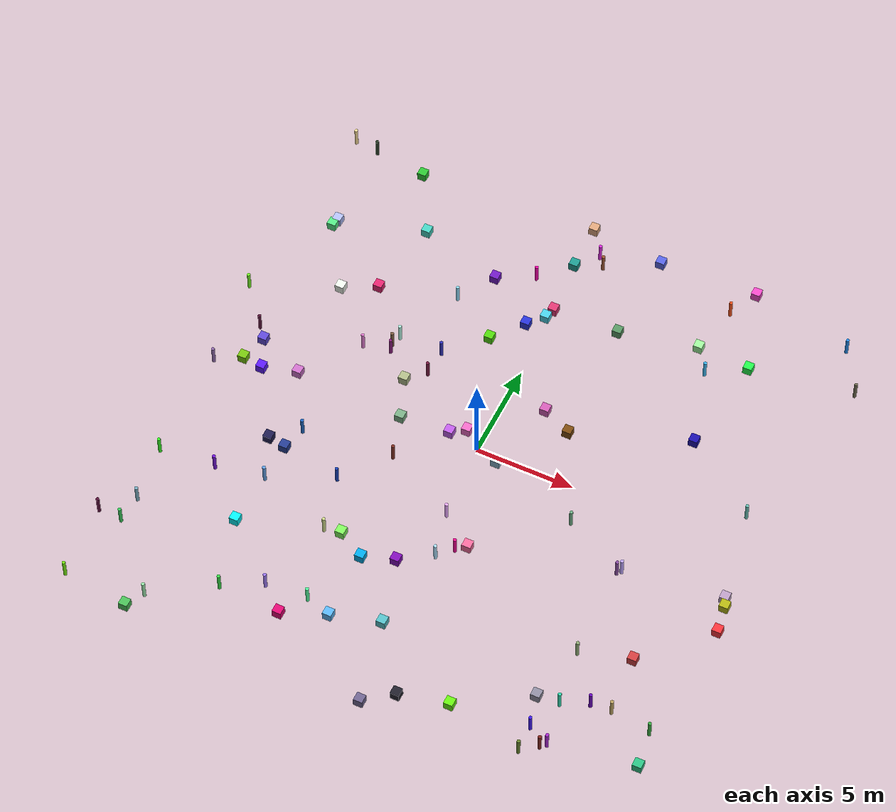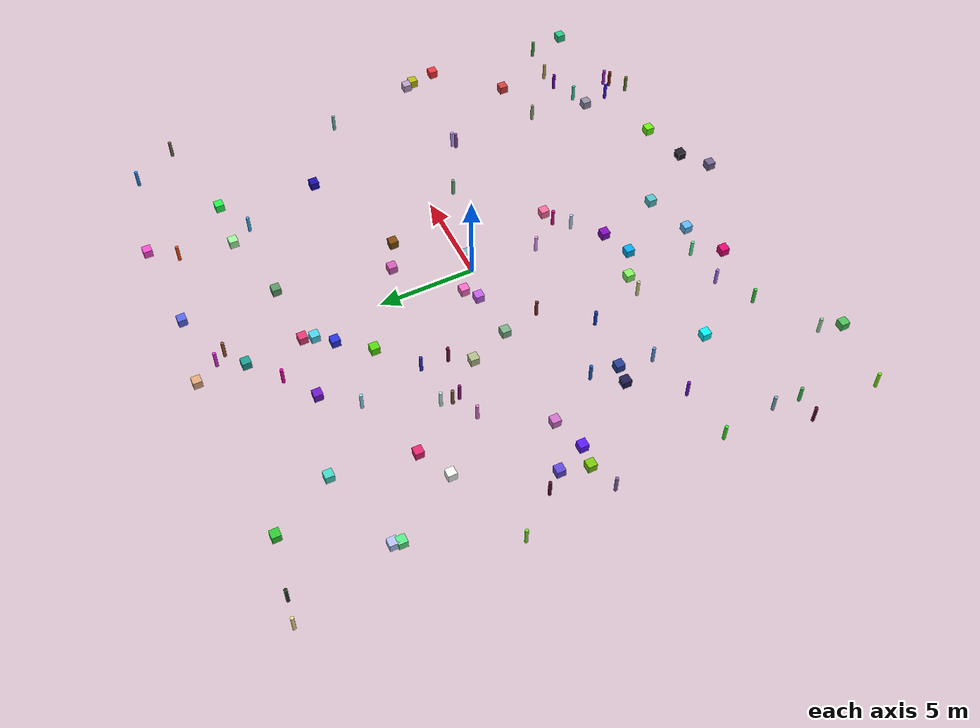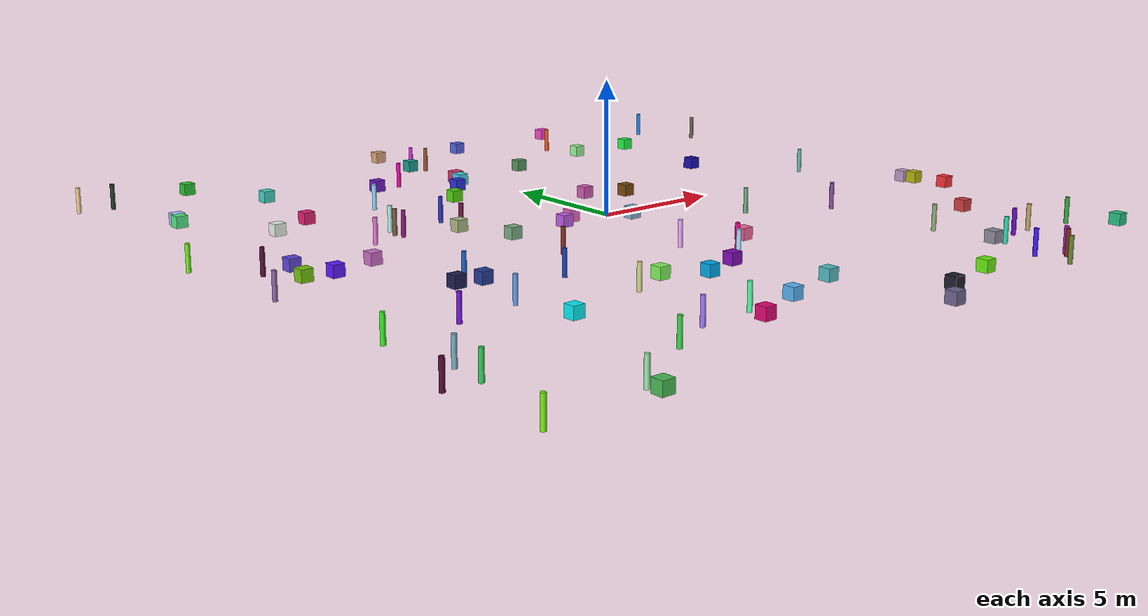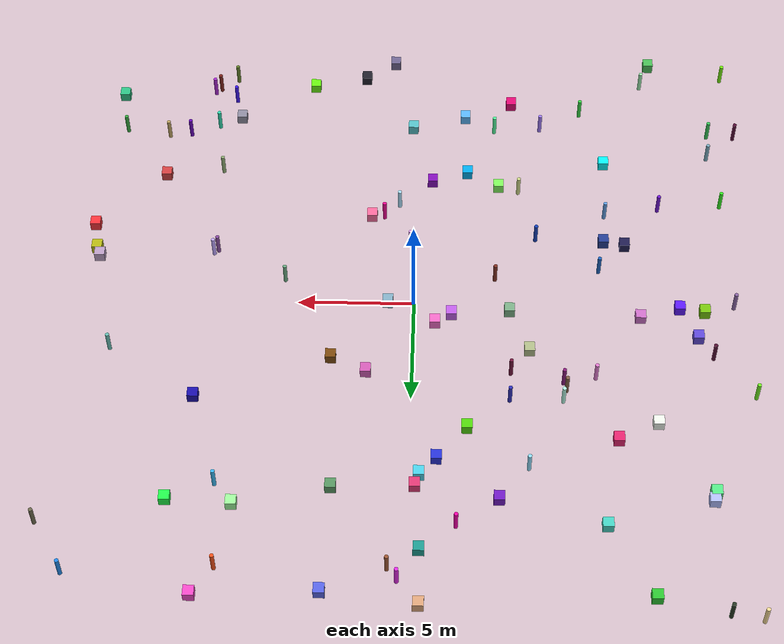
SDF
<sdf version="1.7">
 <world name="warehouse">
  <physics type="ode"><max_step_size>0.003</max_step_size><real_time_factor>1.0</real_time_factor></physics>
  <plugin name="ignition::gazebo::systems::Physics" filename="libignition-gazebo-physics-system.so"/>
  <plugin name="ignition::gazebo::systems::UserCommands" filename="libignition-gazebo-user-commands-system.so"/>
  <plugin name="ignition::gazebo::systems::SceneBroadcaster" filename="libignition-gazebo-scene-broadcaster-system.so"/>
  <plugin name="ignition::gazebo::systems::Sensors" filename="libignition-gazebo-sensors-system.so">
   <render_engine>ogre2</render_engine>
  </plugin>
  <plugin name="ignition::gazebo::systems::Imu" filename="libignition-gazebo-imu-system.so"/>
  <plugin name="ignition::gazebo::systems::NavSat" filename="libignition-gazebo-navsat-system.so"/>
  <scene>
   <ambient>1 1 1 1</ambient>
   <background>0 0 0 1</background>
   <shadows>0</shadows>
   <grid>false</grid>
  </scene>
  <spherical_coordinates>
   <surface_model>EARTH_WGS84</surface_model>
   <world_frame_orientation>ENU</world_frame_orientation>
   <latitude_deg>-22.986687</latitude_deg>
   <longitude_deg>-43.202501</longitude_deg>
   <elevation>0</elevation>
   <heading_deg>0</heading_deg>
  </spherical_coordinates>
  <model name="ground_plane">
   <static>true</static>
   <link name="link">
    <collision name="collision">
     <geometry><plane><normal>0.0 0.0 1</normal><size>1 1</size></plane></geometry>
    </collision>
   </link>
  </model>
  <model name="unit_box_0">
   <static>true</static>
   <pose>-3.74 -6.97 0 0 0 0</pose>
   <link name="link">
    <collision name="collision">
     <geometry><box><size>0.450000 0.450000 0.450000</size></box></geometry>
    </collision>
    <visual name="visual">
     <geometry><box><size>0.450000 0.450000 0.450000</size></box></geometry>
     <material>
      <ambient>0.4980850180369083 0.960499655600825 0.3583159986899397 1</ambient>
      <diffuse>0.4980850180369083 0.960499655600825 0.3583159986899397 1</diffuse>
      <script><uri>file://media/materials/scripts/gazebo.material</uri><name>Gazebo/RandomColor0</name></script>
     </material>
    </visual>
   </link>
  </model>
  <model name="unit_cylinder_0">
   <static>true</static>
   <pose>-10.97 -6.03 0 0 0 0</pose>
   <link name="link">
    <collision name="collision">
     <geometry><cylinder><radius>0.085000</radius><length>1.000000</length></cylinder></geometry>
    </collision>
    <visual name="visual">
     <geometry><cylinder><radius>0.085000</radius><length>1.000000</length></cylinder></geometry>
     <material>
      <ambient>0.4389138975811706 0.0801410722892908 0.8245683421984876 1</ambient>
      <diffuse>0.4389138975811706 0.0801410722892908 0.8245683421984876 1</diffuse>
      <script><uri>file://media/materials/scripts/gazebo.material</uri><name>Gazebo/RandomColor0</name></script>
     </material>
    </visual>
   </link>
  </model>
  <model name="unit_box_1">
   <static>true</static>
   <pose>-1.09 7.88 0 0 0 0</pose>
   <link name="link">
    <collision name="collision">
     <geometry><box><size>0.450000 0.450000 0.450000</size></box></geometry>
    </collision>
    <visual name="visual">
     <geometry><box><size>0.450000 0.450000 0.450000</size></box></geometry>
     <material>
      <ambient>0.15229820428279073 0.19424798606731064 0.8395773356068508 1</ambient>
      <diffuse>0.15229820428279073 0.19424798606731064 0.8395773356068508 1</diffuse>
      <script><uri>file://media/materials/scripts/gazebo.material</uri><name>Gazebo/RandomColor1</name></script>
     </material>
    </visual>
   </link>
  </model>
  <model name="unit_cylinder_1">
   <static>true</static>
   <pose>-13.43 -9.23 0 0 0 0</pose>
   <link name="link">
    <collision name="collision">
     <geometry><cylinder><radius>0.085000</radius><length>1.000000</length></cylinder></geometry>
    </collision>
    <visual name="visual">
     <geometry><cylinder><radius>0.085000</radius><length>1.000000</length></cylinder></geometry>
     <material>
      <ambient>0.4704009460370986 0.6618843798053189 0.7441237253802401 1</ambient>
      <diffuse>0.4704009460370986 0.6618843798053189 0.7441237253802401 1</diffuse>
      <script><uri>file://media/materials/scripts/gazebo.material</uri><name>Gazebo/RandomColor1</name></script>
     </material>
    </visual>
   </link>
  </model>
  <model name="unit_box_2">
   <static>true</static>
   <pose>-8.57 -8.46 0 0 0 0</pose>
   <link name="link">
    <collision name="collision">
     <geometry><box><size>0.450000 0.450000 0.450000</size></box></geometry>
    </collision>
    <visual name="visual">
     <geometry><box><size>0.450000 0.450000 0.450000</size></box></geometry>
     <material>
      <ambient>0.02610628454677022 0.9365514209556366 0.9650196196577847 1</ambient>
      <diffuse>0.02610628454677022 0.9365514209556366 0.9650196196577847 1</diffuse>
      <script><uri>file://media/materials/scripts/gazebo.material</uri><name>Gazebo/RandomColor2</name></script>
     </material>
    </visual>
   </link>
  </model>
  <model name="unit_cylinder_2">
   <static>true</static>
   <pose>10.64 -10.29 0 0 0 0</pose>
   <link name="link">
    <collision name="collision">
     <geometry><cylinder><radius>0.085000</radius><length>1.000000</length></cylinder></geometry>
    </collision>
    <visual name="visual">
     <geometry><cylinder><radius>0.085000</radius><length>1.000000</length></cylinder></geometry>
     <material>
      <ambient>0.3951191309070913 0.024099152062485696 0.7164924057101547 1</ambient>
      <diffuse>0.3951191309070913 0.024099152062485696 0.7164924057101547 1</diffuse>
      <script><uri>file://media/materials/scripts/gazebo.material</uri><name>Gazebo/RandomColor2</name></script>
     </material>
    </visual>
   </link>
  </model>
  <model name="unit_box_3">
   <static>true</static>
   <pose>-4.37 -12.17 0 0 0 0</pose>
   <link name="link">
    <collision name="collision">
     <geometry><box><size>0.450000 0.450000 0.450000</size></box></geometry>
    </collision>
    <visual name="visual">
     <geometry><box><size>0.450000 0.450000 0.450000</size></box></geometry>
     <material>
      <ambient>0.8746587150856394 0.02409011812531292 0.44726136073561196 1</ambient>
      <diffuse>0.8746587150856394 0.02409011812531292 0.44726136073561196 1</diffuse>
      <script><uri>file://media/materials/scripts/gazebo.material</uri><name>Gazebo/RandomColor3</name></script>
     </material>
    </visual>
   </link>
  </model>
  <model name="unit_cylinder_3">
   <static>true</static>
   <pose>8.78 -3.23 0 0 0 0</pose>
   <link name="link">
    <collision name="collision">
     <geometry><cylinder><radius>0.085000</radius><length>1.000000</length></cylinder></geometry>
    </collision>
    <visual name="visual">
     <geometry><cylinder><radius>0.085000</radius><length>1.000000</length></cylinder></geometry>
     <material>
      <ambient>0.5287846025382006 0.2921808749540272 0.6191296932868018 1</ambient>
      <diffuse>0.5287846025382006 0.2921808749540272 0.6191296932868018 1</diffuse>
      <script><uri>file://media/materials/scripts/gazebo.material</uri><name>Gazebo/RandomColor3</name></script>
     </material>
    </visual>
   </link>
  </model>
  <model name="unit_box_4">
   <static>true</static>
   <pose>-0.23 9.23 0 0 0 0</pose>
   <link name="link">
    <collision name="collision">
     <geometry><box><size>0.450000 0.450000 0.450000</size></box></geometry>
    </collision>
    <visual name="visual">
     <geometry><box><size>0.450000 0.450000 0.450000</size></box></geometry>
     <material>
      <ambient>0.8660547508537442 0.21508451391508976 0.4486909282337398 1</ambient>
      <diffuse>0.8660547508537442 0.21508451391508976 0.4486909282337398 1</diffuse>
      <script><uri>file://media/materials/scripts/gazebo.material</uri><name>Gazebo/RandomColor4</name></script>
     </material>
    </visual>
   </link>
  </model>
  <model name="unit_cylinder_4">
   <static>true</static>
   <pose>-6.4 4.69 0 0 0 0</pose>
   <link name="link">
    <collision name="collision">
     <geometry><cylinder><radius>0.085000</radius><length>1.000000</length></cylinder></geometry>
    </collision>
    <visual name="visual">
     <geometry><cylinder><radius>0.085000</radius><length>1.000000</length></cylinder></geometry>
     <material>
      <ambient>0.6947852053141457 0.9475243830453974 0.8768217230580825 1</ambient>
      <diffuse>0.6947852053141457 0.9475243830453974 0.8768217230580825 1</diffuse>
      <script><uri>file://media/materials/scripts/gazebo.material</uri><name>Gazebo/RandomColor4</name></script>
     </material>
    </visual>
   </link>
  </model>
  <model name="unit_box_5">
   <static>true</static>
   <pose>8.29 -11.07 0 0 0 0</pose>
   <link name="link">
    <collision name="collision">
     <geometry><box><size>0.450000 0.450000 0.450000</size></box></geometry>
    </collision>
    <visual name="visual">
     <geometry><box><size>0.450000 0.450000 0.450000</size></box></geometry>
     <material>
      <ambient>0.5556280775581018 0.5461109669091838 0.623188925954208 1</ambient>
      <diffuse>0.5556280775581018 0.5461109669091838 0.623188925954208 1</diffuse>
      <script><uri>file://media/materials/scripts/gazebo.material</uri><name>Gazebo/RandomColor5</name></script>
     </material>
    </visual>
   </link>
  </model>
  <model name="unit_cylinder_5">
   <static>true</static>
   <pose>-14.54 4.34 0 0 0 0</pose>
   <link name="link">
    <collision name="collision">
     <geometry><cylinder><radius>0.085000</radius><length>1.000000</length></cylinder></geometry>
    </collision>
    <visual name="visual">
     <geometry><cylinder><radius>0.085000</radius><length>1.000000</length></cylinder></geometry>
     <material>
      <ambient>0.44332831553045615 0.9268529757130407 0.13489380024273534 1</ambient>
      <diffuse>0.44332831553045615 0.9268529757130407 0.13489380024273534 1</diffuse>
      <script><uri>file://media/materials/scripts/gazebo.material</uri><name>Gazebo/RandomColor5</name></script>
     </material>
    </visual>
   </link>
  </model>
  <model name="unit_box_6">
   <static>true</static>
   <pose>-12.63 0.11 0 0 0 0</pose>
   <link name="link">
    <collision name="collision">
     <geometry><box><size>0.450000 0.450000 0.450000</size></box></geometry>
    </collision>
    <visual name="visual">
     <geometry><box><size>0.450000 0.450000 0.450000</size></box></geometry>
     <material>
      <ambient>0.4659703927487683 0.7641169074565753 0.05321468579074451 1</ambient>
      <diffuse>0.4659703927487683 0.7641169074565753 0.05321468579074451 1</diffuse>
      <script><uri>file://media/materials/scripts/gazebo.material</uri><name>Gazebo/RandomColor6</name></script>
     </material>
    </visual>
   </link>
  </model>
  <model name="unit_cylinder_6">
   <static>true</static>
   <pose>-7.81 3.46 0 0 0 0</pose>
   <link name="link">
    <collision name="collision">
     <geometry><cylinder><radius>0.085000</radius><length>1.000000</length></cylinder></geometry>
    </collision>
    <visual name="visual">
     <geometry><cylinder><radius>0.085000</radius><length>1.000000</length></cylinder></geometry>
     <material>
      <ambient>0.8784691791109419 0.47129200667808324 0.8064720120951105 1</ambient>
      <diffuse>0.8784691791109419 0.47129200667808324 0.8064720120951105 1</diffuse>
      <script><uri>file://media/materials/scripts/gazebo.material</uri><name>Gazebo/RandomColor6</name></script>
     </material>
    </visual>
   </link>
  </model>
  <model name="unit_box_7">
   <static>true</static>
   <pose>13.97 -2.55 0 0 0 0</pose>
   <link name="link">
    <collision name="collision">
     <geometry><box><size>0.450000 0.450000 0.450000</size></box></geometry>
    </collision>
    <visual name="visual">
     <geometry><box><size>0.450000 0.450000 0.450000</size></box></geometry>
     <material>
      <ambient>0.7249337576698359 0.6105177550639291 0.758408008382822 1</ambient>
      <diffuse>0.7249337576698359 0.6105177550639291 0.758408008382822 1</diffuse>
      <script><uri>file://media/materials/scripts/gazebo.material</uri><name>Gazebo/RandomColor7</name></script>
     </material>
    </visual>
   </link>
  </model>
  <model name="unit_cylinder_7">
   <static>true</static>
   <pose>-6.55 4.14 0 0 0 0</pose>
   <link name="link">
    <collision name="collision">
     <geometry><cylinder><radius>0.085000</radius><length>1.000000</length></cylinder></geometry>
    </collision>
    <visual name="visual">
     <geometry><cylinder><radius>0.085000</radius><length>1.000000</length></cylinder></geometry>
     <material>
      <ambient>0.49379655142538703 0.35580831960124626 0.26210022729523175 1</ambient>
      <diffuse>0.49379655142538703 0.35580831960124626 0.26210022729523175 1</diffuse>
      <script><uri>file://media/materials/scripts/gazebo.material</uri><name>Gazebo/RandomColor7</name></script>
     </material>
    </visual>
   </link>
  </model>
  <model name="unit_box_8">
   <static>true</static>
   <pose>-0.39 8.67 0 0 0 0</pose>
   <link name="link">
    <collision name="collision">
     <geometry><box><size>0.450000 0.450000 0.450000</size></box></geometry>
    </collision>
    <visual name="visual">
     <geometry><box><size>0.450000 0.450000 0.450000</size></box></geometry>
     <material>
      <ambient>0.2875771671435562 0.8071056508813194 0.8972424006056334 1</ambient>
      <diffuse>0.2875771671435562 0.8071056508813194 0.8972424006056334 1</diffuse>
      <script><uri>file://media/materials/scripts/gazebo.material</uri><name>Gazebo/RandomColor8</name></script>
     </material>
    </visual>
   </link>
  </model>
  <model name="unit_cylinder_8">
   <static>true</static>
   <pose>8.96 -3.07 0 0 0 0</pose>
   <link name="link">
    <collision name="collision">
     <geometry><cylinder><radius>0.085000</radius><length>1.000000</length></cylinder></geometry>
    </collision>
    <visual name="visual">
     <geometry><cylinder><radius>0.085000</radius><length>1.000000</length></cylinder></geometry>
     <material>
      <ambient>0.7381084247965797 0.6401217386967804 0.9947972658478855 1</ambient>
      <diffuse>0.7381084247965797 0.6401217386967804 0.9947972658478855 1</diffuse>
      <script><uri>file://media/materials/scripts/gazebo.material</uri><name>Gazebo/RandomColor8</name></script>
     </material>
    </visual>
   </link>
  </model>
  <model name="unit_box_9">
   <static>true</static>
   <pose>-2.22 -11.28 0 0 0 0</pose>
   <link name="link">
    <collision name="collision">
     <geometry><box><size>0.450000 0.450000 0.450000</size></box></geometry>
    </collision>
    <visual name="visual">
     <geometry><box><size>0.450000 0.450000 0.450000</size></box></geometry>
     <material>
      <ambient>0.35193521307636255 0.7035614139713785 0.9693010489217475 1</ambient>
      <diffuse>0.35193521307636255 0.7035614139713785 0.9693010489217475 1</diffuse>
      <script><uri>file://media/materials/scripts/gazebo.material</uri><name>Gazebo/RandomColor9</name></script>
     </material>
    </visual>
   </link>
  </model>
  <model name="unit_cylinder_9">
   <static>true</static>
   <pose>9.72 -13.04 0 0 0 0</pose>
   <link name="link">
    <collision name="collision">
     <geometry><cylinder><radius>0.085000</radius><length>1.000000</length></cylinder></geometry>
    </collision>
    <visual name="visual">
     <geometry><cylinder><radius>0.085000</radius><length>1.000000</length></cylinder></geometry>
     <material>
      <ambient>0.6470021254600739 0.1457770489665171 0.7952356764007517 1</ambient>
      <diffuse>0.6470021254600739 0.1457770489665171 0.7952356764007517 1</diffuse>
      <script><uri>file://media/materials/scripts/gazebo.material</uri><name>Gazebo/RandomColor9</name></script>
     </material>
    </visual>
   </link>
  </model>
  <model name="unit_box_10">
   <static>true</static>
   <pose>-0.48 14.66 0 0 0 0</pose>
   <link name="link">
    <collision name="collision">
     <geometry><box><size>0.450000 0.450000 0.450000</size></box></geometry>
    </collision>
    <visual name="visual">
     <geometry><box><size>0.450000 0.450000 0.450000</size></box></geometry>
     <material>
      <ambient>0.8644623813476707 0.6424511392136606 0.4810328838779897 1</ambient>
      <diffuse>0.8644623813476707 0.6424511392136606 0.4810328838779897 1</diffuse>
      <script><uri>file://media/materials/scripts/gazebo.material</uri><name>Gazebo/RandomColor10</name></script>
     </material>
    </visual>
   </link>
  </model>
  <model name="unit_cylinder_10">
   <static>true</static>
   <pose>-1.92 10.89 0 0 0 0</pose>
   <link name="link">
    <collision name="collision">
     <geometry><cylinder><radius>0.085000</radius><length>1.000000</length></cylinder></geometry>
    </collision>
    <visual name="visual">
     <geometry><cylinder><radius>0.085000</radius><length>1.000000</length></cylinder></geometry>
     <material>
      <ambient>0.9525582930420621 0.002756038495029145 0.6536258020727491 1</ambient>
      <diffuse>0.9525582930420621 0.002756038495029145 0.6536258020727491 1</diffuse>
      <script><uri>file://media/materials/scripts/gazebo.material</uri><name>Gazebo/RandomColor10</name></script>
     </material>
    </visual>
   </link>
  </model>
  <model name="unit_box_11">
   <static>true</static>
   <pose>7.12 10.22 0 0 0 0</pose>
   <link name="link">
    <collision name="collision">
     <geometry><box><size>0.450000 0.450000 0.450000</size></box></geometry>
    </collision>
    <visual name="visual">
     <geometry><box><size>0.450000 0.450000 0.450000</size></box></geometry>
     <material>
      <ambient>0.6145988357798 0.961643213783854 0.6059944513285958 1</ambient>
      <diffuse>0.6145988357798 0.961643213783854 0.6059944513285958 1</diffuse>
      <script><uri>file://media/materials/scripts/gazebo.material</uri><name>Gazebo/RandomColor11</name></script>
     </material>
    </visual>
   </link>
  </model>
  <model name="unit_cylinder_11">
   <static>true</static>
   <pose>9.34 -10.85 0 0 0 0</pose>
   <link name="link">
    <collision name="collision">
     <geometry><cylinder><radius>0.085000</radius><length>1.000000</length></cylinder></geometry>
    </collision>
    <visual name="visual">
     <geometry><cylinder><radius>0.085000</radius><length>1.000000</length></cylinder></geometry>
     <material>
      <ambient>0.17809752914333343 0.8258939936243955 0.6662075649570782 1</ambient>
      <diffuse>0.17809752914333343 0.8258939936243955 0.6662075649570782 1</diffuse>
      <script><uri>file://media/materials/scripts/gazebo.material</uri><name>Gazebo/RandomColor11</name></script>
     </material>
    </visual>
   </link>
  </model>
  <model name="unit_box_12">
   <static>true</static>
   <pose>-1.65 0.42 0 0 0 0</pose>
   <link name="link">
    <collision name="collision">
     <geometry><box><size>0.450000 0.450000 0.450000</size></box></geometry>
    </collision>
    <visual name="visual">
     <geometry><box><size>0.450000 0.450000 0.450000</size></box></geometry>
     <material>
      <ambient>0.7455308093309555 0.3605026803975211 0.9002762832812206 1</ambient>
      <diffuse>0.7455308093309555 0.3605026803975211 0.9002762832812206 1</diffuse>
      <script><uri>file://media/materials/scripts/gazebo.material</uri><name>Gazebo/RandomColor12</name></script>
     </material>
    </visual>
   </link>
  </model>
  <model name="unit_cylinder_12">
   <static>true</static>
   <pose>-12.89 2.32 0 0 0 0</pose>
   <link name="link">
    <collision name="collision">
     <geometry><cylinder><radius>0.085000</radius><length>1.000000</length></cylinder></geometry>
    </collision>
    <visual name="visual">
     <geometry><cylinder><radius>0.085000</radius><length>1.000000</length></cylinder></geometry>
     <material>
      <ambient>0.3235637435256604 0.061456666944691096 0.20166742811764038 1</ambient>
      <diffuse>0.3235637435256604 0.061456666944691096 0.20166742811764038 1</diffuse>
      <script><uri>file://media/materials/scripts/gazebo.material</uri><name>Gazebo/RandomColor12</name></script>
     </material>
    </visual>
   </link>
  </model>
  <model name="unit_box_13">
   <static>true</static>
   <pose>11.47 -7.41 0 0 0 0</pose>
   <link name="link">
    <collision name="collision">
     <geometry><box><size>0.450000 0.450000 0.450000</size></box></geometry>
    </collision>
    <visual name="visual">
     <geometry><box><size>0.450000 0.450000 0.450000</size></box></geometry>
     <material>
      <ambient>0.8110253572332984 0.24349753227449822 0.24691038495190987 1</ambient>
      <diffuse>0.8110253572332984 0.24349753227449822 0.24691038495190987 1</diffuse>
      <script><uri>file://media/materials/scripts/gazebo.material</uri><name>Gazebo/RandomColor13</name></script>
     </material>
    </visual>
   </link>
  </model>
  <model name="unit_cylinder_13">
   <static>true</static>
   <pose>9.47 -13.27 0 0 0 0</pose>
   <link name="link">
    <collision name="collision">
     <geometry><cylinder><radius>0.085000</radius><length>1.000000</length></cylinder></geometry>
    </collision>
    <visual name="visual">
     <geometry><cylinder><radius>0.085000</radius><length>1.000000</length></cylinder></geometry>
     <material>
      <ambient>0.49462519191374466 0.1397617091923261 0.10884874237618136 1</ambient>
      <diffuse>0.49462519191374466 0.1397617091923261 0.10884874237618136 1</diffuse>
      <script><uri>file://media/materials/scripts/gazebo.material</uri><name>Gazebo/RandomColor13</name></script>
     </material>
    </visual>
   </link>
  </model>
  <model name="unit_box_14">
   <static>true</static>
   <pose>-12.33 9.7 0 0 0 0</pose>
   <link name="link">
    <collision name="collision">
     <geometry><box><size>0.450000 0.450000 0.450000</size></box></geometry>
    </collision>
    <visual name="visual">
     <geometry><box><size>0.450000 0.450000 0.450000</size></box></geometry>
     <material>
      <ambient>0.6935558128337532 0.7422793944667679 0.9994424598495588 1</ambient>
      <diffuse>0.6935558128337532 0.7422793944667679 0.9994424598495588 1</diffuse>
      <script><uri>file://media/materials/scripts/gazebo.material</uri><name>Gazebo/RandomColor14</name></script>
     </material>
    </visual>
   </link>
  </model>
  <model name="unit_cylinder_14">
   <static>true</static>
   <pose>1.41 -5.36 0 0 0 0</pose>
   <link name="link">
    <collision name="collision">
     <geometry><cylinder><radius>0.085000</radius><length>1.000000</length></cylinder></geometry>
    </collision>
    <visual name="visual">
     <geometry><cylinder><radius>0.085000</radius><length>1.000000</length></cylinder></geometry>
     <material>
      <ambient>0.9128743396111747 0.02162803102222055 0.5512442317872064 1</ambient>
      <diffuse>0.9128743396111747 0.02162803102222055 0.5512442317872064 1</diffuse>
      <script><uri>file://media/materials/scripts/gazebo.material</uri><name>Gazebo/RandomColor14</name></script>
     </material>
    </visual>
   </link>
  </model>
  <model name="unit_box_15">
   <static>true</static>
   <pose>-9.32 -3.59 0 0 0 0</pose>
   <link name="link">
    <collision name="collision">
     <geometry><box><size>0.450000 0.450000 0.450000</size></box></geometry>
    </collision>
    <visual name="visual">
     <geometry><box><size>0.450000 0.450000 0.450000</size></box></geometry>
     <material>
      <ambient>0.12069892018342199 0.10806463234559882 0.31110704592397387 1</ambient>
      <diffuse>0.12069892018342199 0.10806463234559882 0.31110704592397387 1</diffuse>
      <script><uri>file://media/materials/scripts/gazebo.material</uri><name>Gazebo/RandomColor15</name></script>
     </material>
    </visual>
   </link>
  </model>
  <model name="unit_cylinder_15">
   <static>true</static>
   <pose>-3.56 -1.83 0 0 0 0</pose>
   <link name="link">
    <collision name="collision">
     <geometry><cylinder><radius>0.085000</radius><length>1.000000</length></cylinder></geometry>
    </collision>
    <visual name="visual">
     <geometry><cylinder><radius>0.085000</radius><length>1.000000</length></cylinder></geometry>
     <material>
      <ambient>0.4937205321789996 0.18173122081885662 0.13511763427674894 1</ambient>
      <diffuse>0.4937205321789996 0.18173122081885662 0.13511763427674894 1</diffuse>
      <script><uri>file://media/materials/scripts/gazebo.material</uri><name>Gazebo/RandomColor15</name></script>
     </material>
    </visual>
   </link>
  </model>
  <model name="unit_box_16">
   <static>true</static>
   <pose>-0.45 12.2 0 0 0 0</pose>
   <link name="link">
    <collision name="collision">
     <geometry><box><size>0.450000 0.450000 0.450000</size></box></geometry>
    </collision>
    <visual name="visual">
     <geometry><box><size>0.450000 0.450000 0.450000</size></box></geometry>
     <material>
      <ambient>0.11095543232703797 0.6036219379331118 0.5605702950234737 1</ambient>
      <diffuse>0.11095543232703797 0.6036219379331118 0.5605702950234737 1</diffuse>
      <script><uri>file://media/materials/scripts/gazebo.material</uri><name>Gazebo/RandomColor16</name></script>
     </material>
    </visual>
   </link>
  </model>
  <model name="unit_cylinder_16">
   <static>true</static>
   <pose>-4.9 8.08 0 0 0 0</pose>
   <link name="link">
    <collision name="collision">
     <geometry><cylinder><radius>0.085000</radius><length>1.000000</length></cylinder></geometry>
    </collision>
    <visual name="visual">
     <geometry><cylinder><radius>0.085000</radius><length>1.000000</length></cylinder></geometry>
     <material>
      <ambient>0.5542630344734815 0.8489683366086407 0.973796178053389 1</ambient>
      <diffuse>0.5542630344734815 0.8489683366086407 0.973796178053389 1</diffuse>
      <script><uri>file://media/materials/scripts/gazebo.material</uri><name>Gazebo/RandomColor16</name></script>
     </material>
    </visual>
   </link>
  </model>
  <model name="unit_box_17">
   <static>true</static>
   <pose>13.96 -12.43 0 0 0 0</pose>
   <link name="link">
    <collision name="collision">
     <geometry><box><size>0.450000 0.450000 0.450000</size></box></geometry>
    </collision>
    <visual name="visual">
     <geometry><box><size>0.450000 0.450000 0.450000</size></box></geometry>
     <material>
      <ambient>0.16915301006597794 0.7505259792447131 0.5127497678201481 1</ambient>
      <diffuse>0.16915301006597794 0.7505259792447131 0.5127497678201481 1</diffuse>
      <script><uri>file://media/materials/scripts/gazebo.material</uri><name>Gazebo/RandomColor17</name></script>
     </material>
    </visual>
   </link>
  </model>
  <model name="unit_cylinder_17">
   <static>true</static>
   <pose>-8.15 -2.36 0 0 0 0</pose>
   <link name="link">
    <collision name="collision">
     <geometry><cylinder><radius>0.085000</radius><length>1.000000</length></cylinder></geometry>
    </collision>
    <visual name="visual">
     <geometry><cylinder><radius>0.085000</radius><length>1.000000</length></cylinder></geometry>
     <material>
      <ambient>0.10853726732943669 0.3861476694075586 0.7398052743361232 1</ambient>
      <diffuse>0.10853726732943669 0.3861476694075586 0.7398052743361232 1</diffuse>
      <script><uri>file://media/materials/scripts/gazebo.material</uri><name>Gazebo/RandomColor17</name></script>
     </material>
    </visual>
   </link>
  </model>
  <model name="unit_box_18">
   <static>true</static>
   <pose>-8.61 6.83 0 0 0 0</pose>
   <link name="link">
    <collision name="collision">
     <geometry><box><size>0.450000 0.450000 0.450000</size></box></geometry>
    </collision>
    <visual name="visual">
     <geometry><box><size>0.450000 0.450000 0.450000</size></box></geometry>
     <material>
      <ambient>0.8869487226425964 0.1375005252324063 0.431552990861119 1</ambient>
      <diffuse>0.8869487226425964 0.1375005252324063 0.431552990861119 1</diffuse>
      <script><uri>file://media/materials/scripts/gazebo.material</uri><name>Gazebo/RandomColor18</name></script>
     </material>
    </visual>
   </link>
  </model>
  <model name="unit_cylinder_18">
   <static>true</static>
   <pose>13.66 -10.5 0 0 0 0</pose>
   <link name="link">
    <collision name="collision">
     <geometry><cylinder><radius>0.085000</radius><length>1.000000</length></cylinder></geometry>
    </collision>
    <visual name="visual">
     <geometry><cylinder><radius>0.085000</radius><length>1.000000</length></cylinder></geometry>
     <material>
      <ambient>0.208591489377989 0.6374492799857051 0.23825190432938037 1</ambient>
      <diffuse>0.208591489377989 0.6374492799857051 0.23825190432938037 1</diffuse>
      <script><uri>file://media/materials/scripts/gazebo.material</uri><name>Gazebo/RandomColor18</name></script>
     </material>
    </visual>
   </link>
  </model>
  <model name="unit_box_19">
   <static>true</static>
   <pose>-4.17 0.21 0 0 0 0</pose>
   <link name="link">
    <collision name="collision">
     <geometry><box><size>0.450000 0.450000 0.450000</size></box></geometry>
    </collision>
    <visual name="visual">
     <geometry><box><size>0.450000 0.450000 0.450000</size></box></geometry>
     <material>
      <ambient>0.47805622045263474 0.6766579468377217 0.5212968293085998 1</ambient>
      <diffuse>0.47805622045263474 0.6766579468377217 0.5212968293085998 1</diffuse>
      <script><uri>file://media/materials/scripts/gazebo.material</uri><name>Gazebo/RandomColor19</name></script>
     </material>
    </visual>
   </link>
  </model>
  <model name="unit_cylinder_19">
   <static>true</static>
   <pose>7.92 9.09 0 0 0 0</pose>
   <link name="link">
    <collision name="collision">
     <geometry><cylinder><radius>0.085000</radius><length>1.000000</length></cylinder></geometry>
    </collision>
    <visual name="visual">
     <geometry><cylinder><radius>0.085000</radius><length>1.000000</length></cylinder></geometry>
     <material>
      <ambient>0.22212702473033885 0.7042672932400387 0.9354881036511468 1</ambient>
      <diffuse>0.22212702473033885 0.7042672932400387 0.9354881036511468 1</diffuse>
      <script><uri>file://media/materials/scripts/gazebo.material</uri><name>Gazebo/RandomColor19</name></script>
     </material>
    </visual>
   </link>
  </model>
  <model name="unit_box_20">
   <static>true</static>
   <pose>-9.83 0.45 0 0 0 0</pose>
   <link name="link">
    <collision name="collision">
     <geometry><box><size>0.450000 0.450000 0.450000</size></box></geometry>
    </collision>
    <visual name="visual">
     <geometry><box><size>0.450000 0.450000 0.450000</size></box></geometry>
     <material>
      <ambient>0.800013041273511 0.43229751330552413 0.7804690020909605 1</ambient>
      <diffuse>0.800013041273511 0.43229751330552413 0.7804690020909605 1</diffuse>
      <script><uri>file://media/materials/scripts/gazebo.material</uri><name>Gazebo/RandomColor20</name></script>
     </material>
    </visual>
   </link>
  </model>
  <model name="unit_cylinder_20">
   <static>true</static>
   <pose>-12.61 14.69 0 0 0 0</pose>
   <link name="link">
    <collision name="collision">
     <geometry><cylinder><radius>0.085000</radius><length>1.000000</length></cylinder></geometry>
    </collision>
    <visual name="visual">
     <geometry><cylinder><radius>0.085000</radius><length>1.000000</length></cylinder></geometry>
     <material>
      <ambient>0.15415065613971246 0.2190586881499358 0.1428432220085849 1</ambient>
      <diffuse>0.15415065613971246 0.2190586881499358 0.1428432220085849 1</diffuse>
      <script><uri>file://media/materials/scripts/gazebo.material</uri><name>Gazebo/RandomColor20</name></script>
     </material>
    </visual>
   </link>
  </model>
  <model name="unit_box_21">
   <static>true</static>
   <pose>3.47 2.85 0 0 0 0</pose>
   <link name="link">
    <collision name="collision">
     <geometry><box><size>0.450000 0.450000 0.450000</size></box></geometry>
    </collision>
    <visual name="visual">
     <geometry><box><size>0.450000 0.450000 0.450000</size></box></geometry>
     <material>
      <ambient>0.4827835386601903 0.28486479497698036 0.05659831114114833 1</ambient>
      <diffuse>0.4827835386601903 0.28486479497698036 0.05659831114114833 1</diffuse>
      <script><uri>file://media/materials/scripts/gazebo.material</uri><name>Gazebo/RandomColor21</name></script>
     </material>
    </visual>
   </link>
  </model>
  <model name="unit_cylinder_21">
   <static>true</static>
   <pose>8.66 -12.54 0 0 0 0</pose>
   <link name="link">
    <collision name="collision">
     <geometry><cylinder><radius>0.085000</radius><length>1.000000</length></cylinder></geometry>
    </collision>
    <visual name="visual">
     <geometry><cylinder><radius>0.085000</radius><length>1.000000</length></cylinder></geometry>
     <material>
      <ambient>0.23472202786153962 0.08514343118368384 0.9324388474751274 1</ambient>
      <diffuse>0.23472202786153962 0.08514343118368384 0.9324388474751274 1</diffuse>
      <script><uri>file://media/materials/scripts/gazebo.material</uri><name>Gazebo/RandomColor21</name></script>
     </material>
    </visual>
   </link>
  </model>
  <model name="unit_box_22">
   <static>true</static>
   <pose>-0.94 0.89 0 0 0 0</pose>
   <link name="link">
    <collision name="collision">
     <geometry><box><size>0.450000 0.450000 0.450000</size></box></geometry>
    </collision>
    <visual name="visual">
     <geometry><box><size>0.450000 0.450000 0.450000</size></box></geometry>
     <material>
      <ambient>0.9346044560863328 0.4116779133519707 0.7675280531155018 1</ambient>
      <diffuse>0.9346044560863328 0.4116779133519707 0.7675280531155018 1</diffuse>
      <script><uri>file://media/materials/scripts/gazebo.material</uri><name>Gazebo/RandomColor22</name></script>
     </material>
    </visual>
   </link>
  </model>
  <model name="unit_cylinder_22">
   <static>true</static>
   <pose>-13.55 -10.63 0 0 0 0</pose>
   <link name="link">
    <collision name="collision">
     <geometry><cylinder><radius>0.085000</radius><length>1.000000</length></cylinder></geometry>
    </collision>
    <visual name="visual">
     <geometry><cylinder><radius>0.085000</radius><length>1.000000</length></cylinder></geometry>
     <material>
      <ambient>0.2089185752977354 0.7575021185565678 0.3370184298071368 1</ambient>
      <diffuse>0.2089185752977354 0.7575021185565678 0.3370184298071368 1</diffuse>
      <script><uri>file://media/materials/scripts/gazebo.material</uri><name>Gazebo/RandomColor22</name></script>
     </material>
    </visual>
   </link>
  </model>
  <model name="unit_box_23">
   <static>true</static>
   <pose>1.96 3.56 0 0 0 0</pose>
   <link name="link">
    <collision name="collision">
     <geometry><box><size>0.450000 0.450000 0.450000</size></box></geometry>
    </collision>
    <visual name="visual">
     <geometry><box><size>0.450000 0.450000 0.450000</size></box></geometry>
     <material>
      <ambient>0.8173133952369392 0.3542193166256482 0.7041868937527931 1</ambient>
      <diffuse>0.8173133952369392 0.3542193166256482 0.7041868937527931 1</diffuse>
      <script><uri>file://media/materials/scripts/gazebo.material</uri><name>Gazebo/RandomColor23</name></script>
     </material>
    </visual>
   </link>
  </model>
  <model name="unit_cylinder_23">
   <static>true</static>
   <pose>-4.15 4.69 0 0 0 0</pose>
   <link name="link">
    <collision name="collision">
     <geometry><cylinder><radius>0.085000</radius><length>1.000000</length></cylinder></geometry>
    </collision>
    <visual name="visual">
     <geometry><cylinder><radius>0.085000</radius><length>1.000000</length></cylinder></geometry>
     <material>
      <ambient>0.17810956179785042 0.1809651034956592 0.7277209536750412 1</ambient>
      <diffuse>0.17810956179785042 0.1809651034956592 0.7277209536750412 1</diffuse>
      <script><uri>file://media/materials/scripts/gazebo.material</uri><name>Gazebo/RandomColor23</name></script>
     </material>
    </visual>
   </link>
  </model>
  <model name="unit_box_24">
   <static>true</static>
   <pose>-8.39 -3.76 0 0 0 0</pose>
   <link name="link">
    <collision name="collision">
     <geometry><box><size>0.450000 0.450000 0.450000</size></box></geometry>
    </collision>
    <visual name="visual">
     <geometry><box><size>0.450000 0.450000 0.450000</size></box></geometry>
     <material>
      <ambient>0.14072540807198108 0.23468430382870187 0.5680109328304447 1</ambient>
      <diffuse>0.14072540807198108 0.23468430382870187 0.5680109328304447 1</diffuse>
      <script><uri>file://media/materials/scripts/gazebo.material</uri><name>Gazebo/RandomColor24</name></script>
     </material>
    </visual>
   </link>
  </model>
  <model name="unit_cylinder_24">
   <static>true</static>
   <pose>-4.65 -6.97 0 0 0 0</pose>
   <link name="link">
    <collision name="collision">
     <geometry><cylinder><radius>0.085000</radius><length>1.000000</length></cylinder></geometry>
    </collision>
    <visual name="visual">
     <geometry><cylinder><radius>0.085000</radius><length>1.000000</length></cylinder></geometry>
     <material>
      <ambient>0.7976434149158669 0.8337853406166482 0.5272182643346427 1</ambient>
      <diffuse>0.7976434149158669 0.8337853406166482 0.5272182643346427 1</diffuse>
      <script><uri>file://media/materials/scripts/gazebo.material</uri><name>Gazebo/RandomColor24</name></script>
     </material>
    </visual>
   </link>
  </model>
  <model name="unit_box_25">
   <static>true</static>
   <pose>14.37 -4.35 0 0 0 0</pose>
   <link name="link">
    <collision name="collision">
     <geometry><box><size>0.450000 0.450000 0.450000</size></box></geometry>
    </collision>
    <visual name="visual">
     <geometry><box><size>0.450000 0.450000 0.450000</size></box></geometry>
     <material>
      <ambient>0.9642475574671894 0.19675874575342056 0.2238197752322001 1</ambient>
      <diffuse>0.9642475574671894 0.19675874575342056 0.2238197752322001 1</diffuse>
      <script><uri>file://media/materials/scripts/gazebo.material</uri><name>Gazebo/RandomColor25</name></script>
     </material>
    </visual>
   </link>
  </model>
  <model name="unit_cylinder_25">
   <static>true</static>
   <pose>0.39 13.44 0 0 0 0</pose>
   <link name="link">
    <collision name="collision">
     <geometry><cylinder><radius>0.085000</radius><length>1.000000</length></cylinder></geometry>
    </collision>
    <visual name="visual">
     <geometry><cylinder><radius>0.085000</radius><length>1.000000</length></cylinder></geometry>
     <material>
      <ambient>0.8666702591763936 0.15892376307862355 0.8793875946676218 1</ambient>
      <diffuse>0.8666702591763936 0.15892376307862355 0.8793875946676218 1</diffuse>
      <script><uri>file://media/materials/scripts/gazebo.material</uri><name>Gazebo/RandomColor25</name></script>
     </material>
    </visual>
   </link>
  </model>
  <model name="unit_box_26">
   <static>true</static>
   <pose>-9.75 14.14 0 0 0 0</pose>
   <link name="link">
    <collision name="collision">
     <geometry><box><size>0.450000 0.450000 0.450000</size></box></geometry>
    </collision>
    <visual name="visual">
     <geometry><box><size>0.450000 0.450000 0.450000</size></box></geometry>
     <material>
      <ambient>0.17643207013185191 0.7677561358010974 0.19761129052641402 1</ambient>
      <diffuse>0.17643207013185191 0.7677561358010974 0.19761129052641402 1</diffuse>
      <script><uri>file://media/materials/scripts/gazebo.material</uri><name>Gazebo/RandomColor26</name></script>
     </material>
    </visual>
   </link>
  </model>
  <model name="unit_cylinder_26">
   <static>true</static>
   <pose>-8.53 -5.58 0 0 0 0</pose>
   <link name="link">
    <collision name="collision">
     <geometry><cylinder><radius>0.085000</radius><length>1.000000</length></cylinder></geometry>
    </collision>
    <visual name="visual">
     <geometry><cylinder><radius>0.085000</radius><length>1.000000</length></cylinder></geometry>
     <material>
      <ambient>0.3629287924086435 0.6048604145020845 0.8761274533343737 1</ambient>
      <diffuse>0.3629287924086435 0.6048604145020845 0.8761274533343737 1</diffuse>
      <script><uri>file://media/materials/scripts/gazebo.material</uri><name>Gazebo/RandomColor26</name></script>
     </material>
    </visual>
   </link>
  </model>
  <model name="unit_box_27">
   <static>true</static>
   <pose>-2.32 -7.78 0 0 0 0</pose>
   <link name="link">
    <collision name="collision">
     <geometry><box><size>0.450000 0.450000 0.450000</size></box></geometry>
    </collision>
    <visual name="visual">
     <geometry><box><size>0.450000 0.450000 0.450000</size></box></geometry>
     <material>
      <ambient>0.00422555757925458 0.662061601248178 0.9112774507234194 1</ambient>
      <diffuse>0.00422555757925458 0.662061601248178 0.9112774507234194 1</diffuse>
      <script><uri>file://media/materials/scripts/gazebo.material</uri><name>Gazebo/RandomColor27</name></script>
     </material>
    </visual>
   </link>
  </model>
  <model name="unit_cylinder_27">
   <static>true</static>
   <pose>-5.71 -10.92 0 0 0 0</pose>
   <link name="link">
    <collision name="collision">
     <geometry><cylinder><radius>0.085000</radius><length>1.000000</length></cylinder></geometry>
    </collision>
    <visual name="visual">
     <geometry><cylinder><radius>0.085000</radius><length>1.000000</length></cylinder></geometry>
     <material>
      <ambient>0.6066747927778826 0.46567067597783274 0.9475298551158411 1</ambient>
      <diffuse>0.6066747927778826 0.46567067597783274 0.9475298551158411 1</diffuse>
      <script><uri>file://media/materials/scripts/gazebo.material</uri><name>Gazebo/RandomColor27</name></script>
     </material>
    </visual>
   </link>
  </model>
  <model name="unit_box_28">
   <static>true</static>
   <pose>-7.98 10.95 0 0 0 0</pose>
   <link name="link">
    <collision name="collision">
     <geometry><box><size>0.450000 0.450000 0.450000</size></box></geometry>
    </collision>
    <visual name="visual">
     <geometry><box><size>0.450000 0.450000 0.450000</size></box></geometry>
     <material>
      <ambient>0.2679750552921977 0.8173192734437466 0.7523914390481791 1</ambient>
      <diffuse>0.2679750552921977 0.8173192734437466 0.7523914390481791 1</diffuse>
      <script><uri>file://media/materials/scripts/gazebo.material</uri><name>Gazebo/RandomColor28</name></script>
     </material>
    </visual>
   </link>
  </model>
  <model name="unit_cylinder_28">
   <static>true</static>
   <pose>-5.39 -4.15 0 0 0 0</pose>
   <link name="link">
    <collision name="collision">
     <geometry><cylinder><radius>0.085000</radius><length>1.000000</length></cylinder></geometry>
    </collision>
    <visual name="visual">
     <geometry><cylinder><radius>0.085000</radius><length>1.000000</length></cylinder></geometry>
     <material>
      <ambient>0.08267134242650687 0.2432205558076117 0.7102542734132175 1</ambient>
      <diffuse>0.08267134242650687 0.2432205558076117 0.7102542734132175 1</diffuse>
      <script><uri>file://media/materials/scripts/gazebo.material</uri><name>Gazebo/RandomColor28</name></script>
     </material>
    </visual>
   </link>
  </model>
  <model name="unit_box_29">
   <static>true</static>
   <pose>-2.34 6.34 0 0 0 0</pose>
   <link name="link">
    <collision name="collision">
     <geometry><box><size>0.450000 0.450000 0.450000</size></box></geometry>
    </collision>
    <visual name="visual">
     <geometry><box><size>0.450000 0.450000 0.450000</size></box></geometry>
     <material>
      <ambient>0.31713032235451033 0.8335432559940716 0.04722641897218338 1</ambient>
      <diffuse>0.31713032235451033 0.8335432559940716 0.04722641897218338 1</diffuse>
      <script><uri>file://media/materials/scripts/gazebo.material</uri><name>Gazebo/RandomColor29</name></script>
     </material>
    </visual>
   </link>
  </model>
  <model name="unit_cylinder_29">
   <static>true</static>
   <pose>5.68 -1.61 0 0 0 0</pose>
   <link name="link">
    <collision name="collision">
     <geometry><cylinder><radius>0.085000</radius><length>1.000000</length></cylinder></geometry>
    </collision>
    <visual name="visual">
     <geometry><cylinder><radius>0.085000</radius><length>1.000000</length></cylinder></geometry>
     <material>
      <ambient>0.4189912620349502 0.6559453615246396 0.5084581506282869 1</ambient>
      <diffuse>0.4189912620349502 0.6559453615246396 0.5084581506282869 1</diffuse>
      <script><uri>file://media/materials/scripts/gazebo.material</uri><name>Gazebo/RandomColor29</name></script>
     </material>
    </visual>
   </link>
  </model>
  <model name="unit_box_30">
   <static>true</static>
   <pose>9.81 10.06 0 0 0 0</pose>
   <link name="link">
    <collision name="collision">
     <geometry><box><size>0.450000 0.450000 0.450000</size></box></geometry>
    </collision>
    <visual name="visual">
     <geometry><box><size>0.450000 0.450000 0.450000</size></box></geometry>
     <material>
      <ambient>0.13149353250023432 0.9664338605665151 0.2906481966162514 1</ambient>
      <diffuse>0.13149353250023432 0.9664338605665151 0.2906481966162514 1</diffuse>
      <script><uri>file://media/materials/scripts/gazebo.material</uri><name>Gazebo/RandomColor30</name></script>
     </material>
    </visual>
   </link>
  </model>
  <model name="unit_cylinder_30">
   <static>true</static>
   <pose>7.61 13.0 0 0 0 0</pose>
   <link name="link">
    <collision name="collision">
     <geometry><cylinder><radius>0.085000</radius><length>1.000000</length></cylinder></geometry>
    </collision>
    <visual name="visual">
     <geometry><cylinder><radius>0.085000</radius><length>1.000000</length></cylinder></geometry>
     <material>
      <ambient>0.9416585241976446 0.30799764271973473 0.10090097676211518 1</ambient>
      <diffuse>0.9416585241976446 0.30799764271973473 0.10090097676211518 1</diffuse>
      <script><uri>file://media/materials/scripts/gazebo.material</uri><name>Gazebo/RandomColor30</name></script>
     </material>
    </visual>
   </link>
  </model>
  <model name="unit_box_31">
   <static>true</static>
   <pose>-10.29 5.98 0 0 0 0</pose>
   <link name="link">
    <collision name="collision">
     <geometry><box><size>0.450000 0.450000 0.450000</size></box></geometry>
    </collision>
    <visual name="visual">
     <geometry><box><size>0.450000 0.450000 0.450000</size></box></geometry>
     <material>
      <ambient>0.9227478734607951 0.9467508062731496 0.9109724528116844 1</ambient>
      <diffuse>0.9227478734607951 0.9467508062731496 0.9109724528116844 1</diffuse>
      <script><uri>file://media/materials/scripts/gazebo.material</uri><name>Gazebo/RandomColor31</name></script>
     </material>
    </visual>
   </link>
  </model>
  <model name="unit_cylinder_31">
   <static>true</static>
   <pose>-6.44 3.74 0 0 0 0</pose>
   <link name="link">
    <collision name="collision">
     <geometry><cylinder><radius>0.085000</radius><length>1.000000</length></cylinder></geometry>
    </collision>
    <visual name="visual">
     <geometry><cylinder><radius>0.085000</radius><length>1.000000</length></cylinder></geometry>
     <material>
      <ambient>0.5165887355955098 0.09964342692442829 0.4646018939606156 1</ambient>
      <diffuse>0.5165887355955098 0.09964342692442829 0.4646018939606156 1</diffuse>
      <script><uri>file://media/materials/scripts/gazebo.material</uri><name>Gazebo/RandomColor31</name></script>
     </material>
    </visual>
   </link>
  </model>
  <model name="unit_box_32">
   <static>true</static>
   <pose>1.12 -0.18 0 0 0 0</pose>
   <link name="link">
    <collision name="collision">
     <geometry><box><size>0.450000 0.450000 0.450000</size></box></geometry>
    </collision>
    <visual name="visual">
     <geometry><box><size>0.450000 0.450000 0.450000</size></box></geometry>
     <material>
      <ambient>0.5111250520134986 0.6752579512126715 0.7645389159925936 1</ambient>
      <diffuse>0.5111250520134986 0.6752579512126715 0.7645389159925936 1</diffuse>
      <script><uri>file://media/materials/scripts/gazebo.material</uri><name>Gazebo/RandomColor32</name></script>
     </material>
    </visual>
   </link>
  </model>
  <model name="unit_cylinder_32">
   <static>true</static>
   <pose>13.01 2.3 0 0 0 0</pose>
   <link name="link">
    <collision name="collision">
     <geometry><cylinder><radius>0.085000</radius><length>1.000000</length></cylinder></geometry>
    </collision>
    <visual name="visual">
     <geometry><cylinder><radius>0.085000</radius><length>1.000000</length></cylinder></geometry>
     <material>
      <ambient>0.3922970552284478 0.7194021391002101 0.6813596207754475 1</ambient>
      <diffuse>0.3922970552284478 0.7194021391002101 0.6813596207754475 1</diffuse>
      <script><uri>file://media/materials/scripts/gazebo.material</uri><name>Gazebo/RandomColor32</name></script>
     </material>
    </visual>
   </link>
  </model>
  <model name="unit_box_33">
   <static>true</static>
   <pose>-12.26 1.51 0 0 0 0</pose>
   <link name="link">
    <collision name="collision">
     <geometry><box><size>0.450000 0.450000 0.450000</size></box></geometry>
    </collision>
    <visual name="visual">
     <geometry><box><size>0.450000 0.450000 0.450000</size></box></geometry>
     <material>
      <ambient>0.37064481259126947 0.2818050121993063 0.8358296300351596 1</ambient>
      <diffuse>0.37064481259126947 0.2818050121993063 0.8358296300351596 1</diffuse>
      <script><uri>file://media/materials/scripts/gazebo.material</uri><name>Gazebo/RandomColor33</name></script>
     </material>
    </visual>
   </link>
  </model>
  <model name="unit_cylinder_33">
   <static>true</static>
   <pose>-13.99 -0.45 0 0 0 0</pose>
   <link name="link">
    <collision name="collision">
     <geometry><cylinder><radius>0.085000</radius><length>1.000000</length></cylinder></geometry>
    </collision>
    <visual name="visual">
     <geometry><cylinder><radius>0.085000</radius><length>1.000000</length></cylinder></geometry>
     <material>
      <ambient>0.5488593556057717 0.3979863594146389 0.6489646339003239 1</ambient>
      <diffuse>0.5488593556057717 0.3979863594146389 0.6489646339003239 1</diffuse>
      <script><uri>file://media/materials/scripts/gazebo.material</uri><name>Gazebo/RandomColor33</name></script>
     </material>
    </visual>
   </link>
  </model>
  <model name="unit_box_34">
   <static>true</static>
   <pose>9.14 4.99 0 0 0 0</pose>
   <link name="link">
    <collision name="collision">
     <geometry><box><size>0.450000 0.450000 0.450000</size></box></geometry>
    </collision>
    <visual name="visual">
     <geometry><box><size>0.450000 0.450000 0.450000</size></box></geometry>
     <material>
      <ambient>0.10010025601053363 0.05293648956219432 0.6672711665317494 1</ambient>
      <diffuse>0.10010025601053363 0.05293648956219432 0.6672711665317494 1</diffuse>
      <script><uri>file://media/materials/scripts/gazebo.material</uri><name>Gazebo/RandomColor34</name></script>
     </material>
    </visual>
   </link>
  </model>
  <model name="unit_cylinder_34">
   <static>true</static>
   <pose>-13.81 -6.29 0 0 0 0</pose>
   <link name="link">
    <collision name="collision">
     <geometry><cylinder><radius>0.085000</radius><length>1.000000</length></cylinder></geometry>
    </collision>
    <visual name="visual">
     <geometry><cylinder><radius>0.085000</radius><length>1.000000</length></cylinder></geometry>
     <material>
      <ambient>0.20112584838588132 0.9254686084529936 0.12960686188296733 1</ambient>
      <diffuse>0.20112584838588132 0.9254686084529936 0.12960686188296733 1</diffuse>
      <script><uri>file://media/materials/scripts/gazebo.material</uri><name>Gazebo/RandomColor34</name></script>
     </material>
    </visual>
   </link>
  </model>
  <model name="unit_box_35">
   <static>true</static>
   <pose>2.5 -13.76 0 0 0 0</pose>
   <link name="link">
    <collision name="collision">
     <geometry><box><size>0.450000 0.450000 0.450000</size></box></geometry>
    </collision>
    <visual name="visual">
     <geometry><box><size>0.450000 0.450000 0.450000</size></box></geometry>
     <material>
      <ambient>0.12613155469772996 0.11967617979276157 0.16697444322377353 1</ambient>
      <diffuse>0.12613155469772996 0.11967617979276157 0.16697444322377353 1</diffuse>
      <script><uri>file://media/materials/scripts/gazebo.material</uri><name>Gazebo/RandomColor35</name></script>
     </material>
    </visual>
   </link>
  </model>
  <model name="unit_cylinder_35">
   <static>true</static>
   <pose>-7.6 -11.93 0 0 0 0</pose>
   <link name="link">
    <collision name="collision">
     <geometry><cylinder><radius>0.085000</radius><length>1.000000</length></cylinder></geometry>
    </collision>
    <visual name="visual">
     <geometry><cylinder><radius>0.085000</radius><length>1.000000</length></cylinder></geometry>
     <material>
      <ambient>0.20819494379703685 0.821476502362268 0.2672322414408782 1</ambient>
      <diffuse>0.20819494379703685 0.821476502362268 0.2672322414408782 1</diffuse>
      <script><uri>file://media/materials/scripts/gazebo.material</uri><name>Gazebo/RandomColor35</name></script>
     </material>
    </visual>
   </link>
  </model>
  <model name="unit_box_36">
   <static>true</static>
   <pose>0.21 -10.58 0 0 0 0</pose>
   <link name="link">
    <collision name="collision">
     <geometry><box><size>0.450000 0.450000 0.450000</size></box></geometry>
    </collision>
    <visual name="visual">
     <geometry><box><size>0.450000 0.450000 0.450000</size></box></geometry>
     <material>
      <ambient>0.3288396014355276 0.7393559160198355 0.7718647785861189 1</ambient>
      <diffuse>0.3288396014355276 0.7393559160198355 0.7718647785861189 1</diffuse>
      <script><uri>file://media/materials/scripts/gazebo.material</uri><name>Gazebo/RandomColor36</name></script>
     </material>
    </visual>
   </link>
  </model>
  <model name="unit_cylinder_36">
   <static>true</static>
   <pose>-14.77 -10.57 0 0 0 0</pose>
   <link name="link">
    <collision name="collision">
     <geometry><cylinder><radius>0.085000</radius><length>1.000000</length></cylinder></geometry>
    </collision>
    <visual name="visual">
     <geometry><cylinder><radius>0.085000</radius><length>1.000000</length></cylinder></geometry>
     <material>
      <ambient>0.32067003490209345 0.039921720067365274 0.2038701147777071 1</ambient>
      <diffuse>0.32067003490209345 0.039921720067365274 0.2038701147777071 1</diffuse>
      <script><uri>file://media/materials/scripts/gazebo.material</uri><name>Gazebo/RandomColor36</name></script>
     </material>
    </visual>
   </link>
  </model>
  <model name="unit_box_37">
   <static>true</static>
   <pose>3.38 14.16 0 0 0 0</pose>
   <link name="link">
    <collision name="collision">
     <geometry><box><size>0.450000 0.450000 0.450000</size></box></geometry>
    </collision>
    <visual name="visual">
     <geometry><box><size>0.450000 0.450000 0.450000</size></box></geometry>
     <material>
      <ambient>0.3387898691101958 0.38736558731557547 0.8875223111151376 1</ambient>
      <diffuse>0.3387898691101958 0.38736558731557547 0.8875223111151376 1</diffuse>
      <script><uri>file://media/materials/scripts/gazebo.material</uri><name>Gazebo/RandomColor37</name></script>
     </material>
    </visual>
   </link>
  </model>
  <model name="unit_cylinder_37">
   <static>true</static>
   <pose>-10.56 -13.81 0 0 0 0</pose>
   <link name="link">
    <collision name="collision">
     <geometry><cylinder><radius>0.085000</radius><length>1.000000</length></cylinder></geometry>
    </collision>
    <visual name="visual">
     <geometry><cylinder><radius>0.085000</radius><length>1.000000</length></cylinder></geometry>
     <material>
      <ambient>0.593053738875434 0.8847413554462294 0.6590083833456997 1</ambient>
      <diffuse>0.593053738875434 0.8847413554462294 0.6590083833456997 1</diffuse>
      <script><uri>file://media/materials/scripts/gazebo.material</uri><name>Gazebo/RandomColor37</name></script>
     </material>
    </visual>
   </link>
  </model>
  <model name="unit_box_38">
   <static>true</static>
   <pose>-3.66 9.79 0 0 0 0</pose>
   <link name="link">
    <collision name="collision">
     <geometry><box><size>0.450000 0.450000 0.450000</size></box></geometry>
    </collision>
    <visual name="visual">
     <geometry><box><size>0.450000 0.450000 0.450000</size></box></geometry>
     <material>
      <ambient>0.4367081132615912 0.09646312322272055 0.7591621749761531 1</ambient>
      <diffuse>0.4367081132615912 0.09646312322272055 0.7591621749761531 1</diffuse>
      <script><uri>file://media/materials/scripts/gazebo.material</uri><name>Gazebo/RandomColor38</name></script>
     </material>
    </visual>
   </link>
  </model>
  <model name="unit_cylinder_38">
   <static>true</static>
   <pose>-14.46 -14.37 0 0 0 0</pose>
   <link name="link">
    <collision name="collision">
     <geometry><cylinder><radius>0.085000</radius><length>1.000000</length></cylinder></geometry>
    </collision>
    <visual name="visual">
     <geometry><cylinder><radius>0.085000</radius><length>1.000000</length></cylinder></geometry>
     <material>
      <ambient>0.45362352308475906 0.9130312465042271 0.05735154146463328 1</ambient>
      <diffuse>0.45362352308475906 0.9130312465042271 0.05735154146463328 1</diffuse>
      <script><uri>file://media/materials/scripts/gazebo.material</uri><name>Gazebo/RandomColor38</name></script>
     </material>
    </visual>
   </link>
  </model>
  <model name="unit_box_39">
   <static>true</static>
   <pose>8.42 14.38 0 0 0 0</pose>
   <link name="link">
    <collision name="collision">
     <geometry><box><size>0.450000 0.450000 0.450000</size></box></geometry>
    </collision>
    <visual name="visual">
     <geometry><box><size>0.450000 0.450000 0.450000</size></box></geometry>
     <material>
      <ambient>0.9417638609512196 0.2836270793563338 0.7778719784289729 1</ambient>
      <diffuse>0.9417638609512196 0.2836270793563338 0.7778719784289729 1</diffuse>
      <script><uri>file://media/materials/scripts/gazebo.material</uri><name>Gazebo/RandomColor39</name></script>
     </material>
    </visual>
   </link>
  </model>
  <model name="unit_cylinder_39">
   <static>true</static>
   <pose>-13.9 14.89 0 0 0 0</pose>
   <link name="link">
    <collision name="collision">
     <geometry><cylinder><radius>0.085000</radius><length>1.000000</length></cylinder></geometry>
    </collision>
    <visual name="visual">
     <geometry><cylinder><radius>0.085000</radius><length>1.000000</length></cylinder></geometry>
     <material>
      <ambient>0.9626765412690239 0.8458913580526385 0.5844063776457864 1</ambient>
      <diffuse>0.9626765412690239 0.8458913580526385 0.5844063776457864 1</diffuse>
      <script><uri>file://media/materials/scripts/gazebo.material</uri><name>Gazebo/RandomColor39</name></script>
     </material>
    </visual>
   </link>
  </model>
  <model name="unit_box_40">
   <static>true</static>
   <pose>4.92 -13.18 0 0 0 0</pose>
   <link name="link">
    <collision name="collision">
     <geometry><box><size>0.450000 0.450000 0.450000</size></box></geometry>
    </collision>
    <visual name="visual">
     <geometry><box><size>0.450000 0.450000 0.450000</size></box></geometry>
     <material>
      <ambient>0.407985447383044 0.9352767892516779 0.06328202989953735 1</ambient>
      <diffuse>0.407985447383044 0.9352767892516779 0.06328202989953735 1</diffuse>
      <script><uri>file://media/materials/scripts/gazebo.material</uri><name>Gazebo/RandomColor40</name></script>
     </material>
    </visual>
   </link>
  </model>
  <model name="unit_cylinder_40">
   <static>true</static>
   <pose>-3.58 -10.77 0 0 0 0</pose>
   <link name="link">
    <collision name="collision">
     <geometry><cylinder><radius>0.085000</radius><length>1.000000</length></cylinder></geometry>
    </collision>
    <visual name="visual">
     <geometry><cylinder><radius>0.085000</radius><length>1.000000</length></cylinder></geometry>
     <material>
      <ambient>0.32163175201926575 0.9648198209776412 0.611313076969149 1</ambient>
      <diffuse>0.32163175201926575 0.9648198209776412 0.611313076969149 1</diffuse>
      <script><uri>file://media/materials/scripts/gazebo.material</uri><name>Gazebo/RandomColor40</name></script>
     </material>
    </visual>
   </link>
  </model>
  <model name="unit_box_41">
   <static>true</static>
   <pose>-0.74 -7.23 0 0 0 0</pose>
   <link name="link">
    <collision name="collision">
     <geometry><box><size>0.450000 0.450000 0.450000</size></box></geometry>
    </collision>
    <visual name="visual">
     <geometry><box><size>0.450000 0.450000 0.450000</size></box></geometry>
     <material>
      <ambient>0.5038766203907918 0.04914885396404012 0.7161131093334783 1</ambient>
      <diffuse>0.5038766203907918 0.04914885396404012 0.7161131093334783 1</diffuse>
      <script><uri>file://media/materials/scripts/gazebo.material</uri><name>Gazebo/RandomColor41</name></script>
     </material>
    </visual>
   </link>
  </model>
  <model name="unit_cylinder_41">
   <static>true</static>
   <pose>8.7 -13.89 0 0 0 0</pose>
   <link name="link">
    <collision name="collision">
     <geometry><cylinder><radius>0.085000</radius><length>1.000000</length></cylinder></geometry>
    </collision>
    <visual name="visual">
     <geometry><cylinder><radius>0.085000</radius><length>1.000000</length></cylinder></geometry>
     <material>
      <ambient>0.39315117109074016 0.4980364787492796 0.16863949304157622 1</ambient>
      <diffuse>0.39315117109074016 0.4980364787492796 0.16863949304157622 1</diffuse>
      <script><uri>file://media/materials/scripts/gazebo.material</uri><name>Gazebo/RandomColor41</name></script>
     </material>
    </visual>
   </link>
  </model>
  <model name="unit_box_42">
   <static>true</static>
   <pose>1.15 -14.79 0 0 0 0</pose>
   <link name="link">
    <collision name="collision">
     <geometry><box><size>0.450000 0.450000 0.450000</size></box></geometry>
    </collision>
    <visual name="visual">
     <geometry><box><size>0.450000 0.450000 0.450000</size></box></geometry>
     <material>
      <ambient>0.4319506837712087 0.3898605931945892 0.5604981300704471 1</ambient>
      <diffuse>0.4319506837712087 0.3898605931945892 0.5604981300704471 1</diffuse>
      <script><uri>file://media/materials/scripts/gazebo.material</uri><name>Gazebo/RandomColor42</name></script>
     </material>
    </visual>
   </link>
  </model>
  <model name="unit_cylinder_42">
   <static>true</static>
   <pose>11.65 -10.2 0 0 0 0</pose>
   <link name="link">
    <collision name="collision">
     <geometry><cylinder><radius>0.085000</radius><length>1.000000</length></cylinder></geometry>
    </collision>
    <visual name="visual">
     <geometry><cylinder><radius>0.085000</radius><length>1.000000</length></cylinder></geometry>
     <material>
      <ambient>0.7265371909370946 0.622879080170492 0.37219982102966287 1</ambient>
      <diffuse>0.7265371909370946 0.622879080170492 0.37219982102966287 1</diffuse>
      <script><uri>file://media/materials/scripts/gazebo.material</uri><name>Gazebo/RandomColor42</name></script>
     </material>
    </visual>
   </link>
  </model>
  <model name="unit_box_43">
   <static>true</static>
   <pose>-10.98 -14.87 0 0 0 0</pose>
   <link name="link">
    <collision name="collision">
     <geometry><box><size>0.450000 0.450000 0.450000</size></box></geometry>
    </collision>
    <visual name="visual">
     <geometry><box><size>0.450000 0.450000 0.450000</size></box></geometry>
     <material>
      <ambient>0.28628139644671613 0.7360742243861561 0.33680780808601374 1</ambient>
      <diffuse>0.28628139644671613 0.7360742243861561 0.33680780808601374 1</diffuse>
      <script><uri>file://media/materials/scripts/gazebo.material</uri><name>Gazebo/RandomColor43</name></script>
     </material>
    </visual>
   </link>
  </model>
  <model name="unit_cylinder_43">
   <static>true</static>
   <pose>14.99 11.06 0 0 0 0</pose>
   <link name="link">
    <collision name="collision">
     <geometry><cylinder><radius>0.085000</radius><length>1.000000</length></cylinder></geometry>
    </collision>
    <visual name="visual">
     <geometry><cylinder><radius>0.085000</radius><length>1.000000</length></cylinder></geometry>
     <material>
      <ambient>0.4188215348118154 0.39895500879073 0.3034591900540159 1</ambient>
      <diffuse>0.4188215348118154 0.39895500879073 0.3034591900540159 1</diffuse>
      <script><uri>file://media/materials/scripts/gazebo.material</uri><name>Gazebo/RandomColor43</name></script>
     </material>
    </visual>
   </link>
  </model>
  <model name="unit_box_44">
   <static>true</static>
   <pose>3.17 9.35 0 0 0 0</pose>
   <link name="link">
    <collision name="collision">
     <geometry><box><size>0.450000 0.450000 0.450000</size></box></geometry>
    </collision>
    <visual name="visual">
     <geometry><box><size>0.450000 0.450000 0.450000</size></box></geometry>
     <material>
      <ambient>0.33984468914569255 0.5808532109711394 0.380480198035946 1</ambient>
      <diffuse>0.33984468914569255 0.5808532109711394 0.380480198035946 1</diffuse>
      <script><uri>file://media/materials/scripts/gazebo.material</uri><name>Gazebo/RandomColor44</name></script>
     </material>
    </visual>
   </link>
  </model>
  <model name="unit_cylinder_44">
   <static>true</static>
   <pose>0.79 12.9 0 0 0 0</pose>
   <link name="link">
    <collision name="collision">
     <geometry><cylinder><radius>0.085000</radius><length>1.000000</length></cylinder></geometry>
    </collision>
    <visual name="visual">
     <geometry><cylinder><radius>0.085000</radius><length>1.000000</length></cylinder></geometry>
     <material>
      <ambient>0.6071416094204375 0.3306903661872791 0.19986316093028922 1</ambient>
      <diffuse>0.6071416094204375 0.3306903661872791 0.19986316093028922 1</diffuse>
      <script><uri>file://media/materials/scripts/gazebo.material</uri><name>Gazebo/RandomColor44</name></script>
     </material>
    </visual>
   </link>
  </model>
  <model name="unit_box_45">
   <static>true</static>
   <pose>-12.42 9.32 0 0 0 0</pose>
   <link name="link">
    <collision name="collision">
     <geometry><box><size>0.450000 0.450000 0.450000</size></box></geometry>
    </collision>
    <visual name="visual">
     <geometry><box><size>0.450000 0.450000 0.450000</size></box></geometry>
     <material>
      <ambient>0.33005798038085565 0.9048405620769641 0.5219079955429565 1</ambient>
      <diffuse>0.33005798038085565 0.9048405620769641 0.5219079955429565 1</diffuse>
      <script><uri>file://media/materials/scripts/gazebo.material</uri><name>Gazebo/RandomColor45</name></script>
     </material>
    </visual>
   </link>
  </model>
  <model name="unit_cylinder_45">
   <static>true</static>
   <pose>0.2 -3.74 0 0 0 0</pose>
   <link name="link">
    <collision name="collision">
     <geometry><cylinder><radius>0.085000</radius><length>1.000000</length></cylinder></geometry>
    </collision>
    <visual name="visual">
     <geometry><cylinder><radius>0.085000</radius><length>1.000000</length></cylinder></geometry>
     <material>
      <ambient>0.9115891689134331 0.6452294304155727 0.9964823192515747 1</ambient>
      <diffuse>0.9115891689134331 0.6452294304155727 0.9964823192515747 1</diffuse>
      <script><uri>file://media/materials/scripts/gazebo.material</uri><name>Gazebo/RandomColor45</name></script>
     </material>
    </visual>
   </link>
  </model>
  <model name="unit_box_46">
   <static>true</static>
   <pose>14.14 -2.99 0 0 0 0</pose>
   <link name="link">
    <collision name="collision">
     <geometry><box><size>0.450000 0.450000 0.450000</size></box></geometry>
    </collision>
    <visual name="visual">
     <geometry><box><size>0.450000 0.450000 0.450000</size></box></geometry>
     <material>
      <ambient>0.7057256669104568 0.7125694069284318 0.07257350883851332 1</ambient>
      <diffuse>0.7057256669104568 0.7125694069284318 0.07257350883851332 1</diffuse>
      <script><uri>file://media/materials/scripts/gazebo.material</uri><name>Gazebo/RandomColor46</name></script>
     </material>
    </visual>
   </link>
  </model>
  <model name="unit_cylinder_46">
   <static>true</static>
   <pose>13.63 13.35 0 0 0 0</pose>
   <link name="link">
    <collision name="collision">
     <geometry><cylinder><radius>0.085000</radius><length>1.000000</length></cylinder></geometry>
    </collision>
    <visual name="visual">
     <geometry><cylinder><radius>0.085000</radius><length>1.000000</length></cylinder></geometry>
     <material>
      <ambient>0.1263670199067296 0.5240716496614038 0.9005397806193806 1</ambient>
      <diffuse>0.1263670199067296 0.5240716496614038 0.9005397806193806 1</diffuse>
      <script><uri>file://media/materials/scripts/gazebo.material</uri><name>Gazebo/RandomColor46</name></script>
     </material>
    </visual>
   </link>
  </model>
  <model name="unit_box_47">
   <static>true</static>
   <pose>-11.56 -0.05 0 0 0 0</pose>
   <link name="link">
    <collision name="collision">
     <geometry><box><size>0.450000 0.450000 0.450000</size></box></geometry>
    </collision>
    <visual name="visual">
     <geometry><box><size>0.450000 0.450000 0.450000</size></box></geometry>
     <material>
      <ambient>0.3594017185893911 0.0978548930410158 0.9800767573652712 1</ambient>
      <diffuse>0.3594017185893911 0.0978548930410158 0.9800767573652712 1</diffuse>
      <script><uri>file://media/materials/scripts/gazebo.material</uri><name>Gazebo/RandomColor47</name></script>
     </material>
    </visual>
   </link>
  </model>
  <model name="unit_cylinder_47">
   <static>true</static>
   <pose>-4.21 3.29 0 0 0 0</pose>
   <link name="link">
    <collision name="collision">
     <geometry><cylinder><radius>0.085000</radius><length>1.000000</length></cylinder></geometry>
    </collision>
    <visual name="visual">
     <geometry><cylinder><radius>0.085000</radius><length>1.000000</length></cylinder></geometry>
     <material>
      <ambient>0.4418412613696886 0.08033828128409437 0.23577637401644969 1</ambient>
      <diffuse>0.4418412613696886 0.08033828128409437 0.23577637401644969 1</diffuse>
      <script><uri>file://media/materials/scripts/gazebo.material</uri><name>Gazebo/RandomColor47</name></script>
     </material>
    </visual>
   </link>
  </model>
  <model name="unit_box_48">
   <static>true</static>
   <pose>-5.0 2.31 0 0 0 0</pose>
   <link name="link">
    <collision name="collision">
     <geometry><box><size>0.450000 0.450000 0.450000</size></box></geometry>
    </collision>
    <visual name="visual">
     <geometry><box><size>0.450000 0.450000 0.450000</size></box></geometry>
     <material>
      <ambient>0.6847340016780659 0.7264199493073072 0.5311645769341976 1</ambient>
      <diffuse>0.6847340016780659 0.7264199493073072 0.5311645769341976 1</diffuse>
      <script><uri>file://media/materials/scripts/gazebo.material</uri><name>Gazebo/RandomColor48</name></script>
     </material>
    </visual>
   </link>
  </model>
  <model name="unit_cylinder_48">
   <static>true</static>
   <pose>8.94 -8.02 0 0 0 0</pose>
   <link name="link">
    <collision name="collision">
     <geometry><cylinder><radius>0.085000</radius><length>1.000000</length></cylinder></geometry>
    </collision>
    <visual name="visual">
     <geometry><cylinder><radius>0.085000</radius><length>1.000000</length></cylinder></geometry>
     <material>
      <ambient>0.5510068434503518 0.6571691369806901 0.4480726126565505 1</ambient>
      <diffuse>0.5510068434503518 0.6571691369806901 0.4480726126565505 1</diffuse>
      <script><uri>file://media/materials/scripts/gazebo.material</uri><name>Gazebo/RandomColor48</name></script>
     </material>
    </visual>
   </link>
  </model>
  <model name="unit_box_49">
   <static>true</static>
   <pose>1.96 -5.11 0 0 0 0</pose>
   <link name="link">
    <collision name="collision">
     <geometry><box><size>0.450000 0.450000 0.450000</size></box></geometry>
    </collision>
    <visual name="visual">
     <geometry><box><size>0.450000 0.450000 0.450000</size></box></geometry>
     <material>
      <ambient>0.9662165746079892 0.41528185317805855 0.6112616712799032 1</ambient>
      <diffuse>0.9662165746079892 0.41528185317805855 0.6112616712799032 1</diffuse>
      <script><uri>file://media/materials/scripts/gazebo.material</uri><name>Gazebo/RandomColor49</name></script>
     </material>
    </visual>
   </link>
  </model>
  <model name="unit_cylinder_49">
   <static>true</static>
   <pose>0.74 -6.07 0 0 0 0</pose>
   <link name="link">
    <collision name="collision">
     <geometry><cylinder><radius>0.085000</radius><length>1.000000</length></cylinder></geometry>
    </collision>
    <visual name="visual">
     <geometry><cylinder><radius>0.085000</radius><length>1.000000</length></cylinder></geometry>
     <material>
      <ambient>0.656325019165811 0.8541359035041606 0.9668871394533799 1</ambient>
      <diffuse>0.656325019165811 0.8541359035041606 0.9668871394533799 1</diffuse>
      <script><uri>file://media/materials/scripts/gazebo.material</uri><name>Gazebo/RandomColor49</name></script>
     </material>
    </visual>
   </link>
  </model>
 </world>
</sdf>
